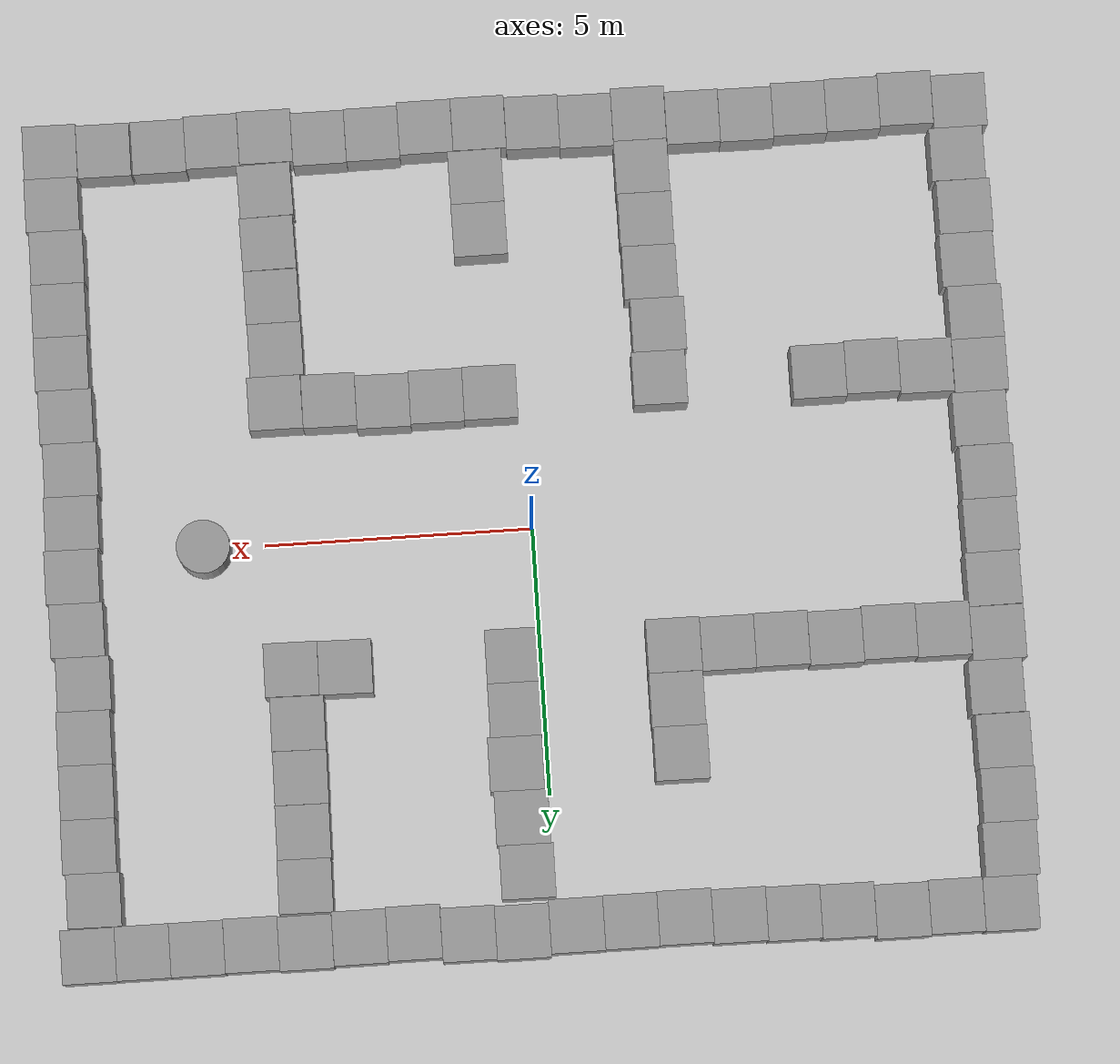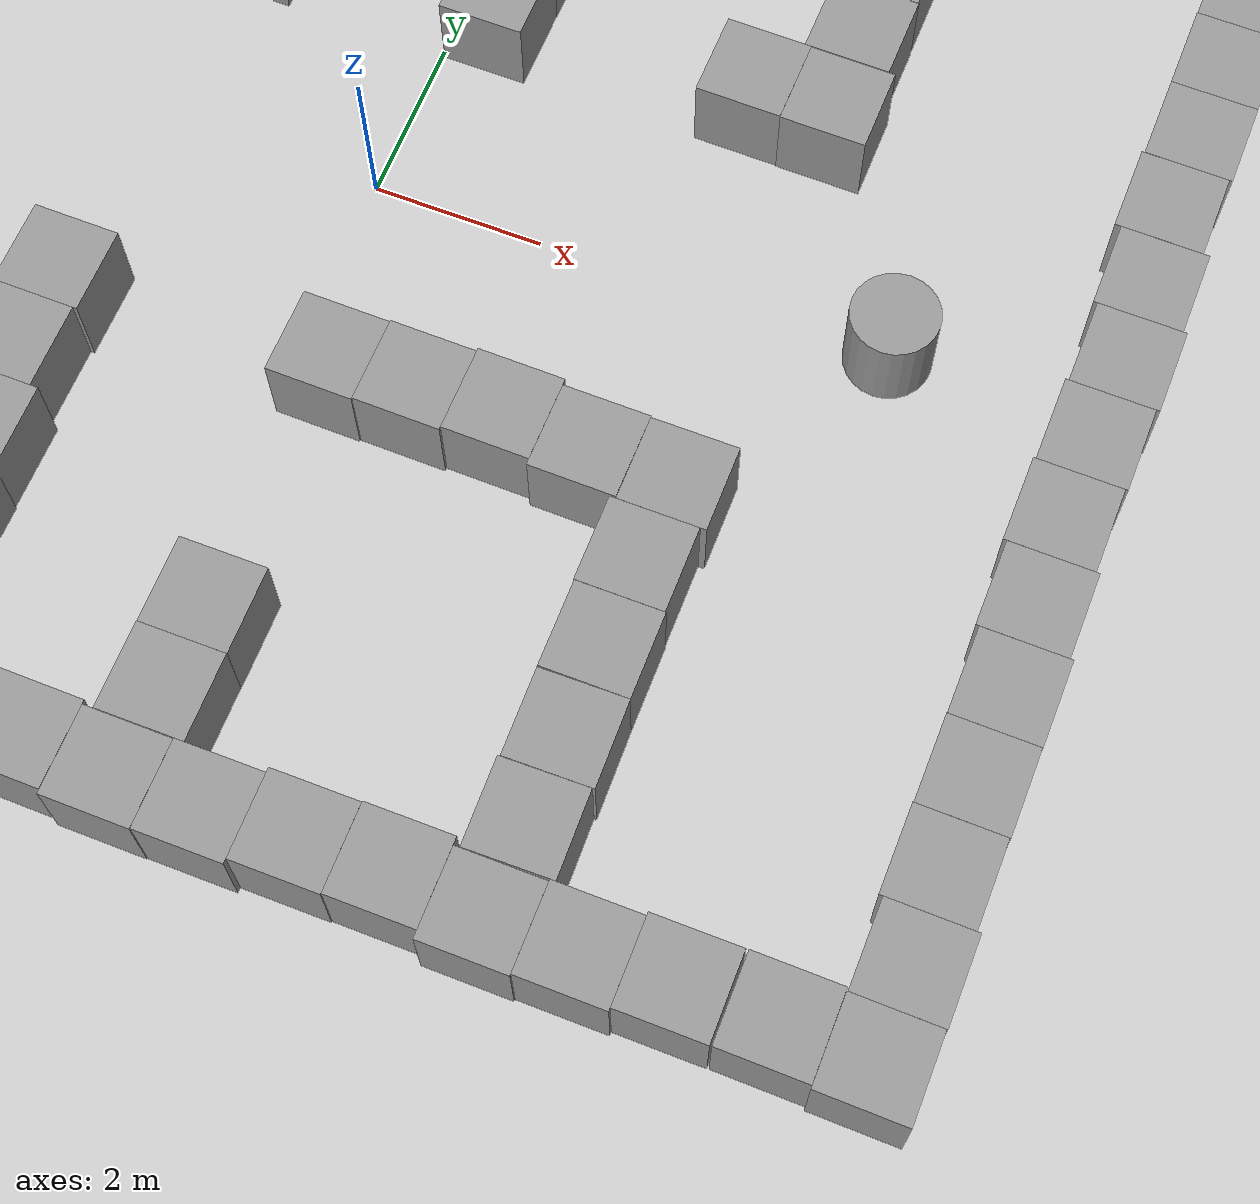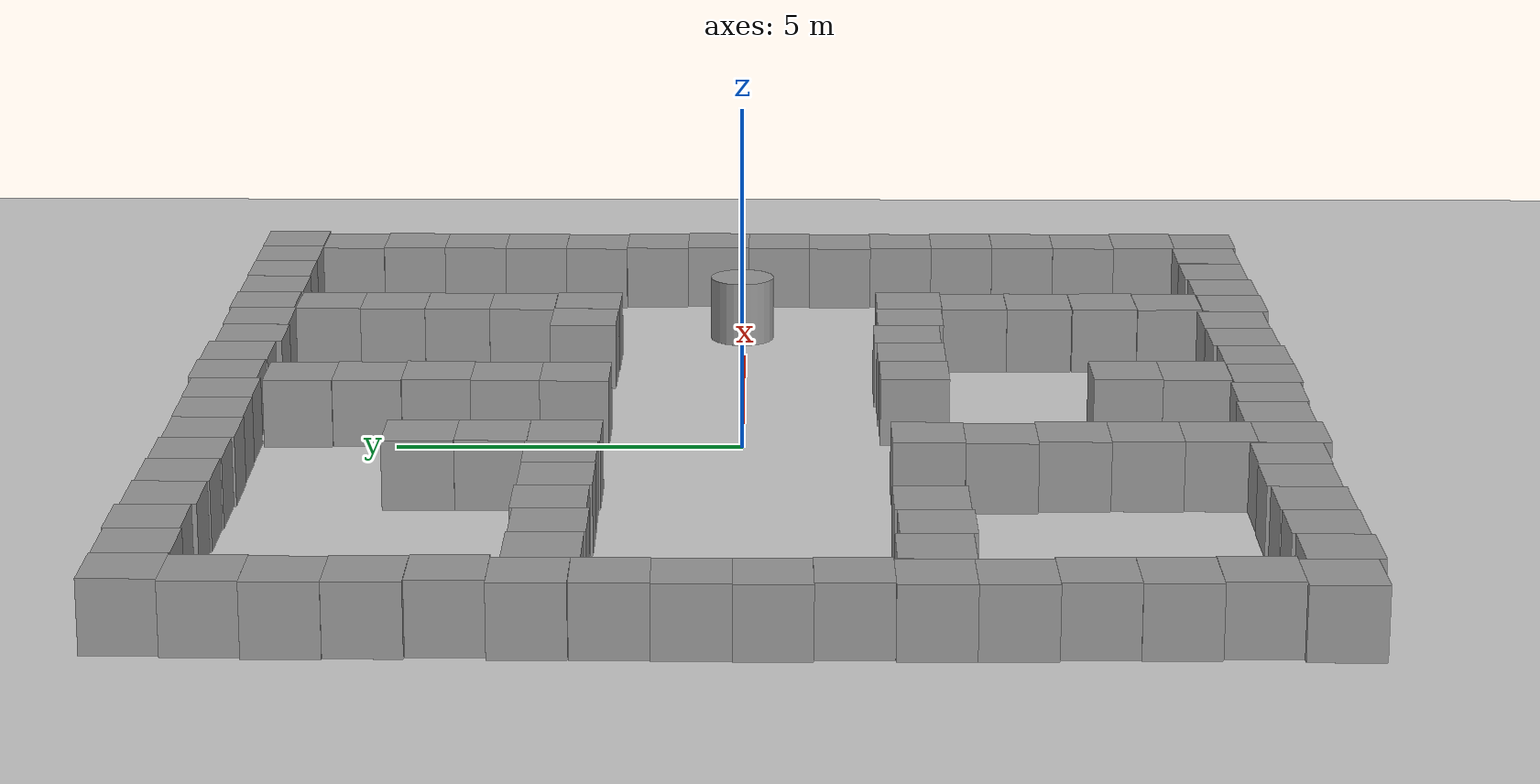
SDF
<sdf version="1.7">
 <world name="default">
  <light name="sun" type="directional">
   <pose>0 0 10 0 -0 0</pose>
   <diffuse>0.8 0.8 0.8 1</diffuse>
   <specular>0.2 0.2 0.2 1</specular>
   <attenuation>
    <range>1000</range>
    <constant>0.9</constant>
    <linear>0.01</linear>
    <quadratic>0.001</quadratic>
   </attenuation>
   <direction>-0.5 0.1 -0.9</direction>
   <spot><inner_angle>0</inner_angle><outer_angle>0</outer_angle><falloff>0</falloff></spot>
  </light>
  <model name="ground_plane">
   <static>1</static>
   <link name="link">
    <collision name="collision">
     <geometry><plane><normal>0 0 1</normal><size>100 100</size></plane></geometry>
     <surface>
      <contact><collide_bitmask>65535</collide_bitmask></contact>
      <friction><ode><mu>100</mu><mu2>50</mu2></ode></friction>
     </surface>
    </collision>
    <visual name="visual">
     <cast_shadows>0</cast_shadows>
     <geometry><plane><normal>0 0 1</normal><size>100 100</size></plane></geometry>
     <material>
      <script><uri>file://media/materials/scripts/gazebo.material</uri><name>Gazebo/Grey</name></script>
     </material>
    </visual>
   </link>
  </model>
  <gravity>0 0 -9.8</gravity>
  <magnetic_field>6e-06 2.3e-05 -4.2e-05</magnetic_field>
  <atmosphere type="adiabatic"/>
  <physics type="ode">
   <max_step_size>0.001</max_step_size>
   <real_time_factor>1</real_time_factor>
   <real_time_update_rate>1000</real_time_update_rate>
  </physics>
  <scene><ambient>0.4 0.4 0.4 1</ambient><background>0.7 0.7 0.7 1</background><shadows>1</shadows></scene>
  <spherical_coordinates>
   <surface_model>EARTH_WGS84</surface_model>
   <latitude_deg>0</latitude_deg>
   <longitude_deg>0</longitude_deg>
   <elevation>0</elevation>
   <heading_deg>0</heading_deg>
  </spherical_coordinates>
  <model name="unit_box">
   <pose>-1.48346 -7.49248 0.499995 1e-05 -0 -0.004181</pose>
   <link name="link">
    <inertial>
     <mass>1</mass>
     <inertia>
      <ixx>0.166667</ixx>
      <ixy>0</ixy>
      <ixz>0</ixz>
      <iyy>0.166667</iyy>
      <iyz>0</iyz>
      <izz>0.166667</izz>
     </inertia>
    </inertial>
    <collision name="collision"><geometry><box><size>1 1 1</size></box></geometry></collision>
    <visual name="visual">
     <geometry><box><size>1 1 1</size></box></geometry>
     <material>
      <script><name>Gazebo/Grey</name><uri>file://media/materials/scripts/gazebo.material</uri></script>
     </material>
    </visual>
   </link>
  </model>
  <model name="unit_box_clone">
   <pose>-0.483452 -7.53028 0.499995 1e-05 0 -0.003876</pose>
   <link name="link">
    <inertial>
     <mass>1</mass>
     <inertia>
      <ixx>0.166667</ixx>
      <ixy>0</ixy>
      <ixz>0</ixz>
      <iyy>0.166667</iyy>
      <iyz>0</iyz>
      <izz>0.166667</izz>
     </inertia>
    </inertial>
    <collision name="collision"><geometry><box><size>1 1 1</size></box></geometry></collision>
    <visual name="visual">
     <geometry><box><size>1 1 1</size></box></geometry>
     <material>
      <script><name>Gazebo/Grey</name><uri>file://media/materials/scripts/gazebo.material</uri></script>
     </material>
    </visual>
   </link>
  </model>
  <model name="unit_box_clone_0">
   <pose>0.519092 -7.5801 0.499995 -0 -1e-05 0.001579</pose>
   <link name="link">
    <inertial>
     <mass>1</mass>
     <inertia>
      <ixx>0.166667</ixx>
      <ixy>0</ixy>
      <ixz>0</ixz>
      <iyy>0.166667</iyy>
      <iyz>0</iyz>
      <izz>0.166667</izz>
     </inertia>
    </inertial>
    <collision name="collision"><geometry><box><size>1 1 1</size></box></geometry></collision>
    <visual name="visual">
     <geometry><box><size>1 1 1</size></box></geometry>
     <material>
      <script><name>Gazebo/Grey</name><uri>file://media/materials/scripts/gazebo.material</uri></script>
     </material>
    </visual>
   </link>
  </model>
  <model name="unit_box_clone_1">
   <pose>1.52066 -7.56872 0.499995 0 1e-05 0.004781</pose>
   <link name="link">
    <inertial>
     <mass>1</mass>
     <inertia>
      <ixx>0.166667</ixx>
      <ixy>0</ixy>
      <ixz>0</ixz>
      <iyy>0.166667</iyy>
      <iyz>0</iyz>
      <izz>0.166667</izz>
     </inertia>
    </inertial>
    <collision name="collision"><geometry><box><size>1 1 1</size></box></geometry></collision>
    <visual name="visual">
     <geometry><box><size>1 1 1</size></box></geometry>
     <material>
      <script><name>Gazebo/Grey</name><uri>file://media/materials/scripts/gazebo.material</uri></script>
     </material>
    </visual>
   </link>
  </model>
  <model name="unit_box_clone_2">
   <pose>2.52041 -7.50619 0.5 0 -0 0.004764</pose>
   <link name="link">
    <inertial>
     <mass>1</mass>
     <inertia>
      <ixx>0.166667</ixx>
      <ixy>0</ixy>
      <ixz>0</ixz>
      <iyy>0.166667</iyy>
      <iyz>0</iyz>
      <izz>0.166667</izz>
     </inertia>
    </inertial>
    <collision name="collision"><geometry><box><size>1 1 1</size></box></geometry></collision>
    <visual name="visual">
     <geometry><box><size>1 1 1</size></box></geometry>
     <material>
      <script><name>Gazebo/Grey</name><uri>file://media/materials/scripts/gazebo.material</uri></script>
     </material>
    </visual>
   </link>
  </model>
  <model name="unit_box_clone_3">
   <pose>3.521 -7.4896 0.499995 -1e-05 0 0.003476</pose>
   <link name="link">
    <inertial>
     <mass>1</mass>
     <inertia>
      <ixx>0.166667</ixx>
      <ixy>0</ixy>
      <ixz>0</ixz>
      <iyy>0.166667</iyy>
      <iyz>0</iyz>
      <izz>0.166667</izz>
     </inertia>
    </inertial>
    <collision name="collision"><geometry><box><size>1 1 1</size></box></geometry></collision>
    <visual name="visual">
     <geometry><box><size>1 1 1</size></box></geometry>
     <material>
      <script><name>Gazebo/Grey</name><uri>file://media/materials/scripts/gazebo.material</uri></script>
     </material>
    </visual>
   </link>
  </model>
  <model name="unit_box_clone_4">
   <pose>4.52182 -7.58155 0.5 0 -0 0.002312</pose>
   <link name="link">
    <inertial>
     <mass>1</mass>
     <inertia>
      <ixx>0.166667</ixx>
      <ixy>0</ixy>
      <ixz>0</ixz>
      <iyy>0.166667</iyy>
      <iyz>0</iyz>
      <izz>0.166667</izz>
     </inertia>
    </inertial>
    <collision name="collision"><geometry><box><size>1 1 1</size></box></geometry></collision>
    <visual name="visual">
     <geometry><box><size>1 1 1</size></box></geometry>
     <material>
      <script><name>Gazebo/Grey</name><uri>file://media/materials/scripts/gazebo.material</uri></script>
     </material>
    </visual>
   </link>
  </model>
  <model name="unit_box_clone_5">
   <pose>4.57544 -6.56698 0.499995 0 1e-05 0.020932</pose>
   <link name="link">
    <inertial>
     <mass>1</mass>
     <inertia>
      <ixx>0.166667</ixx>
      <ixy>0</ixy>
      <ixz>0</ixz>
      <iyy>0.166667</iyy>
      <iyz>0</iyz>
      <izz>0.166667</izz>
     </inertia>
    </inertial>
    <collision name="collision"><geometry><box><size>1 1 1</size></box></geometry></collision>
    <visual name="visual">
     <geometry><box><size>1 1 1</size></box></geometry>
     <material>
      <script><name>Gazebo/Grey</name><uri>file://media/materials/scripts/gazebo.material</uri></script>
     </material>
    </visual>
   </link>
  </model>
  <model name="unit_box_clone_6">
   <pose>4.5842 -5.56396 0.499995 0 -1e-05 0.016221</pose>
   <link name="link">
    <inertial>
     <mass>1</mass>
     <inertia>
      <ixx>0.166667</ixx>
      <ixy>0</ixy>
      <ixz>0</ixz>
      <iyy>0.166667</iyy>
      <iyz>0</iyz>
      <izz>0.166667</izz>
     </inertia>
    </inertial>
    <collision name="collision"><geometry><box><size>1 1 1</size></box></geometry></collision>
    <visual name="visual">
     <geometry><box><size>1 1 1</size></box></geometry>
     <material>
      <script><name>Gazebo/Grey</name><uri>file://media/materials/scripts/gazebo.material</uri></script>
     </material>
    </visual>
   </link>
  </model>
  <model name="unit_box_clone_7">
   <pose>4.57346 -4.5573 0.499995 -0 -1e-05 0.003007</pose>
   <link name="link">
    <inertial>
     <mass>1</mass>
     <inertia>
      <ixx>0.166667</ixx>
      <ixy>0</ixy>
      <ixz>0</ixz>
      <iyy>0.166667</iyy>
      <iyz>0</iyz>
      <izz>0.166667</izz>
     </inertia>
    </inertial>
    <collision name="collision"><geometry><box><size>1 1 1</size></box></geometry></collision>
    <visual name="visual">
     <geometry><box><size>1 1 1</size></box></geometry>
     <material>
      <script><name>Gazebo/Grey</name><uri>file://media/materials/scripts/gazebo.material</uri></script>
     </material>
    </visual>
   </link>
  </model>
  <model name="unit_box_clone_8">
   <pose>4.56116 -3.55637 0.499995 -1e-05 0 0.001132</pose>
   <link name="link">
    <inertial>
     <mass>1</mass>
     <inertia>
      <ixx>0.166667</ixx>
      <ixy>0</ixy>
      <ixz>0</ixz>
      <iyy>0.166667</iyy>
      <iyz>0</iyz>
      <izz>0.166667</izz>
     </inertia>
    </inertial>
    <collision name="collision"><geometry><box><size>1 1 1</size></box></geometry></collision>
    <visual name="visual">
     <geometry><box><size>1 1 1</size></box></geometry>
     <material>
      <script><name>Gazebo/Grey</name><uri>file://media/materials/scripts/gazebo.material</uri></script>
     </material>
    </visual>
   </link>
  </model>
  <model name="unit_box_clone_9">
   <pose>4.63155 -2.55598 0.5 0 -0 0.000421</pose>
   <link name="link">
    <inertial>
     <mass>1</mass>
     <inertia>
      <ixx>0.166667</ixx>
      <ixy>0</ixy>
      <ixz>0</ixz>
      <iyy>0.166667</iyy>
      <iyz>0</iyz>
      <izz>0.166667</izz>
     </inertia>
    </inertial>
    <collision name="collision"><geometry><box><size>1 1 1</size></box></geometry></collision>
    <visual name="visual">
     <geometry><box><size>1 1 1</size></box></geometry>
     <material>
      <script><name>Gazebo/Grey</name><uri>file://media/materials/scripts/gazebo.material</uri></script>
     </material>
    </visual>
   </link>
  </model>
  <model name="unit_box_clone_14">
   <pose>4.62729 2.42572 0.499995 0 1e-05 -0.011577</pose>
   <link name="link">
    <inertial>
     <mass>1</mass>
     <inertia>
      <ixx>0.166667</ixx>
      <ixy>0</ixy>
      <ixz>0</ixz>
      <iyy>0.166667</iyy>
      <iyz>0</iyz>
      <izz>0.166667</izz>
     </inertia>
    </inertial>
    <collision name="collision"><geometry><box><size>1 1 1</size></box></geometry></collision>
    <visual name="visual">
     <geometry><box><size>1 1 1</size></box></geometry>
     <material>
      <script><name>Gazebo/Grey</name><uri>file://media/materials/scripts/gazebo.material</uri></script>
     </material>
    </visual>
   </link>
  </model>
  <model name="unit_box_clone_15">
   <pose>4.56324 3.43446 0.499995 -1e-05 -0 -0.01434</pose>
   <link name="link">
    <inertial>
     <mass>1</mass>
     <inertia>
      <ixx>0.166667</ixx>
      <ixy>0</ixy>
      <ixz>0</ixz>
      <iyy>0.166667</iyy>
      <iyz>0</iyz>
      <izz>0.166667</izz>
     </inertia>
    </inertial>
    <collision name="collision"><geometry><box><size>1 1 1</size></box></geometry></collision>
    <visual name="visual">
     <geometry><box><size>1 1 1</size></box></geometry>
     <material>
      <script><name>Gazebo/Grey</name><uri>file://media/materials/scripts/gazebo.material</uri></script>
     </material>
    </visual>
   </link>
  </model>
  <model name="unit_box_clone_16">
   <pose>4.56989 4.436 0.499995 0 1e-05 -0.01189</pose>
   <link name="link">
    <inertial>
     <mass>1</mass>
     <inertia>
      <ixx>0.166667</ixx>
      <ixy>0</ixy>
      <ixz>0</ixz>
      <iyy>0.166667</iyy>
      <iyz>0</iyz>
      <izz>0.166667</izz>
     </inertia>
    </inertial>
    <collision name="collision"><geometry><box><size>1 1 1</size></box></geometry></collision>
    <visual name="visual">
     <geometry><box><size>1 1 1</size></box></geometry>
     <material>
      <script><name>Gazebo/Grey</name><uri>file://media/materials/scripts/gazebo.material</uri></script>
     </material>
    </visual>
   </link>
  </model>
  <model name="unit_box_clone_17">
   <pose>4.58635 5.43745 0.5 0 0 -0.010937</pose>
   <link name="link">
    <inertial>
     <mass>1</mass>
     <inertia>
      <ixx>0.166667</ixx>
      <ixy>0</ixy>
      <ixz>0</ixz>
      <iyy>0.166667</iyy>
      <iyz>0</iyz>
      <izz>0.166667</izz>
     </inertia>
    </inertial>
    <collision name="collision"><geometry><box><size>1 1 1</size></box></geometry></collision>
    <visual name="visual">
     <geometry><box><size>1 1 1</size></box></geometry>
     <material>
      <script><name>Gazebo/Grey</name><uri>file://media/materials/scripts/gazebo.material</uri></script>
     </material>
    </visual>
   </link>
  </model>
  <model name="unit_box_clone_18">
   <pose>4.60841 6.4373 0.499995 1e-05 -0 -0.010852</pose>
   <link name="link">
    <inertial>
     <mass>1</mass>
     <inertia>
      <ixx>0.166667</ixx>
      <ixy>0</ixy>
      <ixz>0</ixz>
      <iyy>0.166667</iyy>
      <iyz>0</iyz>
      <izz>0.166667</izz>
     </inertia>
    </inertial>
    <collision name="collision"><geometry><box><size>1 1 1</size></box></geometry></collision>
    <visual name="visual">
     <geometry><box><size>1 1 1</size></box></geometry>
     <material>
      <script><name>Gazebo/Grey</name><uri>file://media/materials/scripts/gazebo.material</uri></script>
     </material>
    </visual>
   </link>
  </model>
  <model name="unit_box_clone_19">
   <pose>4.66485 7.47334 0.499995 0 -1e-05 -0.000855</pose>
   <link name="link">
    <inertial>
     <mass>1</mass>
     <inertia>
      <ixx>0.166667</ixx>
      <ixy>0</ixy>
      <ixz>0</ixz>
      <iyy>0.166667</iyy>
      <iyz>0</iyz>
      <izz>0.166667</izz>
     </inertia>
    </inertial>
    <collision name="collision"><geometry><box><size>1 1 1</size></box></geometry></collision>
    <visual name="visual">
     <geometry><box><size>1 1 1</size></box></geometry>
     <material>
      <script><name>Gazebo/Grey</name><uri>file://media/materials/scripts/gazebo.material</uri></script>
     </material>
    </visual>
   </link>
  </model>
  <model name="unit_box_clone_20">
   <pose>3.66379 7.44276 0.499995 1e-05 -0 0.001076</pose>
   <link name="link">
    <inertial>
     <mass>1</mass>
     <inertia>
      <ixx>0.166667</ixx>
      <ixy>0</ixy>
      <ixz>0</ixz>
      <iyy>0.166667</iyy>
      <iyz>0</iyz>
      <izz>0.166667</izz>
     </inertia>
    </inertial>
    <collision name="collision"><geometry><box><size>1 1 1</size></box></geometry></collision>
    <visual name="visual">
     <geometry><box><size>1 1 1</size></box></geometry>
     <material>
      <script><name>Gazebo/Grey</name><uri>file://media/materials/scripts/gazebo.material</uri></script>
     </material>
    </visual>
   </link>
  </model>
  <model name="unit_box_clone_21">
   <pose>2.6637 7.42174 0.499995 -1e-05 0 0.000863</pose>
   <link name="link">
    <inertial>
     <mass>1</mass>
     <inertia>
      <ixx>0.166667</ixx>
      <ixy>0</ixy>
      <ixz>0</ixz>
      <iyy>0.166667</iyy>
      <iyz>0</iyz>
      <izz>0.166667</izz>
     </inertia>
    </inertial>
    <collision name="collision"><geometry><box><size>1 1 1</size></box></geometry></collision>
    <visual name="visual">
     <geometry><box><size>1 1 1</size></box></geometry>
     <material>
      <script><name>Gazebo/Grey</name><uri>file://media/materials/scripts/gazebo.material</uri></script>
     </material>
    </visual>
   </link>
  </model>
  <model name="unit_box_clone_22">
   <pose>1.66264 7.50897 0.499995 -1e-05 0 0.000387</pose>
   <link name="link">
    <inertial>
     <mass>1</mass>
     <inertia>
      <ixx>0.166667</ixx>
      <ixy>0</ixy>
      <ixz>0</ixz>
      <iyy>0.166667</iyy>
      <iyz>0</iyz>
      <izz>0.166667</izz>
     </inertia>
    </inertial>
    <collision name="collision"><geometry><box><size>1 1 1</size></box></geometry></collision>
    <visual name="visual">
     <geometry><box><size>1 1 1</size></box></geometry>
     <material>
      <script><name>Gazebo/Grey</name><uri>file://media/materials/scripts/gazebo.material</uri></script>
     </material>
    </visual>
   </link>
  </model>
  <model name="unit_box_clone_23">
   <pose>0.662513 7.53388 0.499995 1e-05 -0 0.000217</pose>
   <link name="link">
    <inertial>
     <mass>1</mass>
     <inertia>
      <ixx>0.166667</ixx>
      <ixy>0</ixy>
      <ixz>0</ixz>
      <iyy>0.166667</iyy>
      <iyz>0</iyz>
      <izz>0.166667</izz>
     </inertia>
    </inertial>
    <collision name="collision"><geometry><box><size>1 1 1</size></box></geometry></collision>
    <visual name="visual">
     <geometry><box><size>1 1 1</size></box></geometry>
     <material>
      <script><name>Gazebo/Grey</name><uri>file://media/materials/scripts/gazebo.material</uri></script>
     </material>
    </visual>
   </link>
  </model>
  <model name="unit_box_clone_24">
   <pose>-0.337977 7.47713 0.499995 -1e-05 -0 0.00065</pose>
   <link name="link">
    <inertial>
     <mass>1</mass>
     <inertia>
      <ixx>0.166667</ixx>
      <ixy>0</ixy>
      <ixz>0</ixz>
      <iyy>0.166667</iyy>
      <iyz>0</iyz>
      <izz>0.166667</izz>
     </inertia>
    </inertial>
    <collision name="collision"><geometry><box><size>1 1 1</size></box></geometry></collision>
    <visual name="visual">
     <geometry><box><size>1 1 1</size></box></geometry>
     <material>
      <script><name>Gazebo/Grey</name><uri>file://media/materials/scripts/gazebo.material</uri></script>
     </material>
    </visual>
   </link>
  </model>
  <model name="unit_box_clone_25">
   <pose>-1.33802 7.46853 0.5 0 -0 0.000596</pose>
   <link name="link">
    <inertial>
     <mass>1</mass>
     <inertia>
      <ixx>0.166667</ixx>
      <ixy>0</ixy>
      <ixz>0</ixz>
      <iyy>0.166667</iyy>
      <iyz>0</iyz>
      <izz>0.166667</izz>
     </inertia>
    </inertial>
    <collision name="collision"><geometry><box><size>1 1 1</size></box></geometry></collision>
    <visual name="visual">
     <geometry><box><size>1 1 1</size></box></geometry>
     <material>
      <script><name>Gazebo/Grey</name><uri>file://media/materials/scripts/gazebo.material</uri></script>
     </material>
    </visual>
   </link>
  </model>
  <model name="unit_box_clone_26">
   <pose>-2.33802 7.4561 0.5 0 -0 0.000584</pose>
   <link name="link">
    <inertial>
     <mass>1</mass>
     <inertia>
      <ixx>0.166667</ixx>
      <ixy>0</ixy>
      <ixz>0</ixz>
      <iyy>0.166667</iyy>
      <iyz>0</iyz>
      <izz>0.166667</izz>
     </inertia>
    </inertial>
    <collision name="collision"><geometry><box><size>1 1 1</size></box></geometry></collision>
    <visual name="visual">
     <geometry><box><size>1 1 1</size></box></geometry>
     <material>
      <script><name>Gazebo/Grey</name><uri>file://media/materials/scripts/gazebo.material</uri></script>
     </material>
    </visual>
   </link>
  </model>
  <model name="unit_box_clone_27">
   <pose>-3.33817 7.49082 0.5 0 -0 0.000326</pose>
   <link name="link">
    <inertial>
     <mass>1</mass>
     <inertia>
      <ixx>0.166667</ixx>
      <ixy>0</ixy>
      <ixz>0</ixz>
      <iyy>0.166667</iyy>
      <iyz>0</iyz>
      <izz>0.166667</izz>
     </inertia>
    </inertial>
    <collision name="collision"><geometry><box><size>1 1 1</size></box></geometry></collision>
    <visual name="visual">
     <geometry><box><size>1 1 1</size></box></geometry>
     <material>
      <script><name>Gazebo/Grey</name><uri>file://media/materials/scripts/gazebo.material</uri></script>
     </material>
    </visual>
   </link>
  </model>
  <model name="unit_box_clone_28">
   <pose>-4.33829 7.51118 0.5 0 -0 8.9e-05</pose>
   <link name="link">
    <inertial>
     <mass>1</mass>
     <inertia>
      <ixx>0.166667</ixx>
      <ixy>0</ixy>
      <ixz>0</ixz>
      <iyy>0.166667</iyy>
      <iyz>0</iyz>
      <izz>0.166667</izz>
     </inertia>
    </inertial>
    <collision name="collision"><geometry><box><size>1 1 1</size></box></geometry></collision>
    <visual name="visual">
     <geometry><box><size>1 1 1</size></box></geometry>
     <material>
      <script><name>Gazebo/Grey</name><uri>file://media/materials/scripts/gazebo.material</uri></script>
     </material>
    </visual>
   </link>
  </model>
  <model name="unit_box_clone_29">
   <pose>-5.3383 7.53597 0.499995 1e-05 0 6.8e-05</pose>
   <link name="link">
    <inertial>
     <mass>1</mass>
     <inertia>
      <ixx>0.166667</ixx>
      <ixy>0</ixy>
      <ixz>0</ixz>
      <iyy>0.166667</iyy>
      <iyz>0</iyz>
      <izz>0.166667</izz>
     </inertia>
    </inertial>
    <collision name="collision"><geometry><box><size>1 1 1</size></box></geometry></collision>
    <visual name="visual">
     <geometry><box><size>1 1 1</size></box></geometry>
     <material>
      <script><name>Gazebo/Grey</name><uri>file://media/materials/scripts/gazebo.material</uri></script>
     </material>
    </visual>
   </link>
  </model>
  <model name="unit_box_clone_30">
   <pose>-6.33833 7.60037 0.499995 1e-05 -0 1.4e-05</pose>
   <link name="link">
    <inertial>
     <mass>1</mass>
     <inertia>
      <ixx>0.166667</ixx>
      <ixy>0</ixy>
      <ixz>0</ixz>
      <iyy>0.166667</iyy>
      <iyz>0</iyz>
      <izz>0.166667</izz>
     </inertia>
    </inertial>
    <collision name="collision"><geometry><box><size>1 1 1</size></box></geometry></collision>
    <visual name="visual">
     <geometry><box><size>1 1 1</size></box></geometry>
     <material>
      <script><name>Gazebo/Grey</name><uri>file://media/materials/scripts/gazebo.material</uri></script>
     </material>
    </visual>
   </link>
  </model>
  <model name="unit_box_clone_31">
   <pose>-7.3384 7.57702 0.499995 0 -1e-05 -9.3e-05</pose>
   <link name="link">
    <inertial>
     <mass>1</mass>
     <inertia>
      <ixx>0.166667</ixx>
      <ixy>0</ixy>
      <ixz>0</ixz>
      <iyy>0.166667</iyy>
      <iyz>0</iyz>
      <izz>0.166667</izz>
     </inertia>
    </inertial>
    <collision name="collision"><geometry><box><size>1 1 1</size></box></geometry></collision>
    <visual name="visual">
     <geometry><box><size>1 1 1</size></box></geometry>
     <material>
      <script><name>Gazebo/Grey</name><uri>file://media/materials/scripts/gazebo.material</uri></script>
     </material>
    </visual>
   </link>
  </model>
  <model name="unit_box_clone_32">
   <pose>-8.33868 7.5929 0.499995 0 1e-05 -0.000708</pose>
   <link name="link">
    <inertial>
     <mass>1</mass>
     <inertia>
      <ixx>0.166667</ixx>
      <ixy>0</ixy>
      <ixz>0</ixz>
      <iyy>0.166667</iyy>
      <iyz>0</iyz>
      <izz>0.166667</izz>
     </inertia>
    </inertial>
    <collision name="collision"><geometry><box><size>1 1 1</size></box></geometry></collision>
    <visual name="visual">
     <geometry><box><size>1 1 1</size></box></geometry>
     <material>
      <script><name>Gazebo/Grey</name><uri>file://media/materials/scripts/gazebo.material</uri></script>
     </material>
    </visual>
   </link>
  </model>
  <model name="unit_box_clone_33">
   <pose>-8.40776 6.59292 0.499995 0 1e-05 -0.000748</pose>
   <link name="link">
    <inertial>
     <mass>1</mass>
     <inertia>
      <ixx>0.166667</ixx>
      <ixy>0</ixy>
      <ixz>0</ixz>
      <iyy>0.166667</iyy>
      <iyz>0</iyz>
      <izz>0.166667</izz>
     </inertia>
    </inertial>
    <collision name="collision"><geometry><box><size>1 1 1</size></box></geometry></collision>
    <visual name="visual">
     <geometry><box><size>1 1 1</size></box></geometry>
     <material>
      <script><name>Gazebo/Grey</name><uri>file://media/materials/scripts/gazebo.material</uri></script>
     </material>
    </visual>
   </link>
  </model>
  <model name="unit_box_clone_34">
   <pose>-8.44819 5.59252 0.5 -0 -0 -0.001683</pose>
   <link name="link">
    <inertial>
     <mass>1</mass>
     <inertia>
      <ixx>0.166667</ixx>
      <ixy>0</ixy>
      <ixz>0</ixz>
      <iyy>0.166667</iyy>
      <iyz>0</iyz>
      <izz>0.166667</izz>
     </inertia>
    </inertial>
    <collision name="collision"><geometry><box><size>1 1 1</size></box></geometry></collision>
    <visual name="visual">
     <geometry><box><size>1 1 1</size></box></geometry>
     <material>
      <script><name>Gazebo/Grey</name><uri>file://media/materials/scripts/gazebo.material</uri></script>
     </material>
    </visual>
   </link>
  </model>
  <model name="unit_box_clone_35">
   <pose>-8.43292 4.59249 0.499995 0 1e-05 -0.001692</pose>
   <link name="link">
    <inertial>
     <mass>1</mass>
     <inertia>
      <ixx>0.166667</ixx>
      <ixy>0</ixy>
      <ixz>0</ixz>
      <iyy>0.166667</iyy>
      <iyz>0</iyz>
      <izz>0.166667</izz>
     </inertia>
    </inertial>
    <collision name="collision"><geometry><box><size>1 1 1</size></box></geometry></collision>
    <visual name="visual">
     <geometry><box><size>1 1 1</size></box></geometry>
     <material>
      <script><name>Gazebo/Grey</name><uri>file://media/materials/scripts/gazebo.material</uri></script>
     </material>
    </visual>
   </link>
  </model>
  <model name="unit_box_clone_36">
   <pose>-8.37185 3.5869 0.499995 1e-05 -0 0.002115</pose>
   <link name="link">
    <inertial>
     <mass>1</mass>
     <inertia>
      <ixx>0.166667</ixx>
      <ixy>0</ixy>
      <ixz>0</ixz>
      <iyy>0.166667</iyy>
      <iyz>0</iyz>
      <izz>0.166667</izz>
     </inertia>
    </inertial>
    <collision name="collision"><geometry><box><size>1 1 1</size></box></geometry></collision>
    <visual name="visual">
     <geometry><box><size>1 1 1</size></box></geometry>
     <material>
      <script><name>Gazebo/Grey</name><uri>file://media/materials/scripts/gazebo.material</uri></script>
     </material>
    </visual>
   </link>
  </model>
  <model name="unit_box_clone_37">
   <pose>-8.4713 2.58632 0.499995 0 -1e-05 0.002251</pose>
   <link name="link">
    <inertial>
     <mass>1</mass>
     <inertia>
      <ixx>0.166667</ixx>
      <ixy>0</ixy>
      <ixz>0</ixz>
      <iyy>0.166667</iyy>
      <iyz>0</iyz>
      <izz>0.166667</izz>
     </inertia>
    </inertial>
    <collision name="collision"><geometry><box><size>1 1 1</size></box></geometry></collision>
    <visual name="visual">
     <geometry><box><size>1 1 1</size></box></geometry>
     <material>
      <script><name>Gazebo/Grey</name><uri>file://media/materials/scripts/gazebo.material</uri></script>
     </material>
    </visual>
   </link>
  </model>
  <model name="unit_box_clone_38">
   <pose>-8.46655 1.5814 0.499995 1e-05 -0 0.009421</pose>
   <link name="link">
    <inertial>
     <mass>1</mass>
     <inertia>
      <ixx>0.166667</ixx>
      <ixy>0</ixy>
      <ixz>0</ixz>
      <iyy>0.166667</iyy>
      <iyz>0</iyz>
      <izz>0.166667</izz>
     </inertia>
    </inertial>
    <collision name="collision"><geometry><box><size>1 1 1</size></box></geometry></collision>
    <visual name="visual">
     <geometry><box><size>1 1 1</size></box></geometry>
     <material>
      <script><name>Gazebo/Grey</name><uri>file://media/materials/scripts/gazebo.material</uri></script>
     </material>
    </visual>
   </link>
  </model>
  <model name="unit_box_clone_39">
   <pose>-8.49089 0.58107 0.499995 -1e-05 0 0.009286</pose>
   <link name="link">
    <inertial>
     <mass>1</mass>
     <inertia>
      <ixx>0.166667</ixx>
      <ixy>0</ixy>
      <ixz>0</ixz>
      <iyy>0.166667</iyy>
      <iyz>0</iyz>
      <izz>0.166667</izz>
     </inertia>
    </inertial>
    <collision name="collision"><geometry><box><size>1 1 1</size></box></geometry></collision>
    <visual name="visual">
     <geometry><box><size>1 1 1</size></box></geometry>
     <material>
      <script><name>Gazebo/Grey</name><uri>file://media/materials/scripts/gazebo.material</uri></script>
     </material>
    </visual>
   </link>
  </model>
  <model name="unit_box_clone_40">
   <pose>-8.50342 -0.419544 0.499995 1e-05 0 0.008373</pose>
   <link name="link">
    <inertial>
     <mass>1</mass>
     <inertia>
      <ixx>0.166667</ixx>
      <ixy>0</ixy>
      <ixz>0</ixz>
      <iyy>0.166667</iyy>
      <iyz>0</iyz>
      <izz>0.166667</izz>
     </inertia>
    </inertial>
    <collision name="collision"><geometry><box><size>1 1 1</size></box></geometry></collision>
    <visual name="visual">
     <geometry><box><size>1 1 1</size></box></geometry>
     <material>
      <script><name>Gazebo/Grey</name><uri>file://media/materials/scripts/gazebo.material</uri></script>
     </material>
    </visual>
   </link>
  </model>
  <model name="unit_box_clone_41">
   <pose>-8.44531 -1.42065 0.499995 0 1e-05 0.005312</pose>
   <link name="link">
    <inertial>
     <mass>1</mass>
     <inertia>
      <ixx>0.166667</ixx>
      <ixy>0</ixy>
      <ixz>0</ixz>
      <iyy>0.166667</iyy>
      <iyz>0</iyz>
      <izz>0.166667</izz>
     </inertia>
    </inertial>
    <collision name="collision"><geometry><box><size>1 1 1</size></box></geometry></collision>
    <visual name="visual">
     <geometry><box><size>1 1 1</size></box></geometry>
     <material>
      <script><name>Gazebo/Grey</name><uri>file://media/materials/scripts/gazebo.material</uri></script>
     </material>
    </visual>
   </link>
  </model>
  <model name="unit_box_clone_42">
   <pose>-8.50894 -2.42112 0.499995 0 -1e-05 0.005258</pose>
   <link name="link">
    <inertial>
     <mass>1</mass>
     <inertia>
      <ixx>0.166667</ixx>
      <ixy>0</ixy>
      <ixz>0</ixz>
      <iyy>0.166667</iyy>
      <iyz>0</iyz>
      <izz>0.166667</izz>
     </inertia>
    </inertial>
    <collision name="collision"><geometry><box><size>1 1 1</size></box></geometry></collision>
    <visual name="visual">
     <geometry><box><size>1 1 1</size></box></geometry>
     <material>
      <script><name>Gazebo/Grey</name><uri>file://media/materials/scripts/gazebo.material</uri></script>
     </material>
    </visual>
   </link>
  </model>
  <model name="unit_box_clone_43">
   <pose>-8.50524 -3.42113 0.499995 -0 -1e-05 0.005234</pose>
   <link name="link">
    <inertial>
     <mass>1</mass>
     <inertia>
      <ixx>0.166667</ixx>
      <ixy>0</ixy>
      <ixz>0</ixz>
      <iyy>0.166667</iyy>
      <iyz>0</iyz>
      <izz>0.166667</izz>
     </inertia>
    </inertial>
    <collision name="collision"><geometry><box><size>1 1 1</size></box></geometry></collision>
    <visual name="visual">
     <geometry><box><size>1 1 1</size></box></geometry>
     <material>
      <script><name>Gazebo/Grey</name><uri>file://media/materials/scripts/gazebo.material</uri></script>
     </material>
    </visual>
   </link>
  </model>
  <model name="unit_box_clone_44">
   <pose>-8.42681 -4.42082 0.499995 -0 -1e-05 0.005078</pose>
   <link name="link">
    <inertial>
     <mass>1</mass>
     <inertia>
      <ixx>0.166667</ixx>
      <ixy>0</ixy>
      <ixz>0</ixz>
      <iyy>0.166667</iyy>
      <iyz>0</iyz>
      <izz>0.166667</izz>
     </inertia>
    </inertial>
    <collision name="collision"><geometry><box><size>1 1 1</size></box></geometry></collision>
    <visual name="visual">
     <geometry><box><size>1 1 1</size></box></geometry>
     <material>
      <script><name>Gazebo/Grey</name><uri>file://media/materials/scripts/gazebo.material</uri></script>
     </material>
    </visual>
   </link>
  </model>
  <model name="unit_box_clone_45">
   <pose>-8.44626 -5.42149 0.499995 0 -1e-05 0.00396</pose>
   <link name="link">
    <inertial>
     <mass>1</mass>
     <inertia>
      <ixx>0.166667</ixx>
      <ixy>0</ixy>
      <ixz>0</ixz>
      <iyy>0.166667</iyy>
      <iyz>0</iyz>
      <izz>0.166667</izz>
     </inertia>
    </inertial>
    <collision name="collision"><geometry><box><size>1 1 1</size></box></geometry></collision>
    <visual name="visual">
     <geometry><box><size>1 1 1</size></box></geometry>
     <material>
      <script><name>Gazebo/Grey</name><uri>file://media/materials/scripts/gazebo.material</uri></script>
     </material>
    </visual>
   </link>
  </model>
  <model name="unit_box_clone_46">
   <pose>-8.38158 -6.42358 0.499995 -0 -1e-05 -0.000724</pose>
   <link name="link">
    <inertial>
     <mass>1</mass>
     <inertia>
      <ixx>0.166667</ixx>
      <ixy>0</ixy>
      <ixz>0</ixz>
      <iyy>0.166667</iyy>
      <iyz>0</iyz>
      <izz>0.166667</izz>
     </inertia>
    </inertial>
    <collision name="collision"><geometry><box><size>1 1 1</size></box></geometry></collision>
    <visual name="visual">
     <geometry><box><size>1 1 1</size></box></geometry>
     <material>
      <script><name>Gazebo/Grey</name><uri>file://media/materials/scripts/gazebo.material</uri></script>
     </material>
    </visual>
   </link>
  </model>
  <model name="unit_box_clone_47">
   <pose>-8.48809 -7.4237 0.499995 -1e-05 -0 -0.001166</pose>
   <link name="link">
    <inertial>
     <mass>1</mass>
     <inertia>
      <ixx>0.166667</ixx>
      <ixy>0</ixy>
      <ixz>0</ixz>
      <iyy>0.166667</iyy>
      <iyz>0</iyz>
      <izz>0.166667</izz>
     </inertia>
    </inertial>
    <collision name="collision"><geometry><box><size>1 1 1</size></box></geometry></collision>
    <visual name="visual">
     <geometry><box><size>1 1 1</size></box></geometry>
     <material>
      <script><name>Gazebo/Grey</name><uri>file://media/materials/scripts/gazebo.material</uri></script>
     </material>
    </visual>
   </link>
  </model>
  <model name="unit_box_clone_48">
   <pose>-7.48748 -7.52979 0.5 0 0 -0.003001</pose>
   <link name="link">
    <inertial>
     <mass>1</mass>
     <inertia>
      <ixx>0.166667</ixx>
      <ixy>0</ixy>
      <ixz>0</ixz>
      <iyy>0.166667</iyy>
      <iyz>0</iyz>
      <izz>0.166667</izz>
     </inertia>
    </inertial>
    <collision name="collision"><geometry><box><size>1 1 1</size></box></geometry></collision>
    <visual name="visual">
     <geometry><box><size>1 1 1</size></box></geometry>
     <material>
      <script><name>Gazebo/Grey</name><uri>file://media/materials/scripts/gazebo.material</uri></script>
     </material>
    </visual>
   </link>
  </model>
  <model name="unit_box_clone_49">
   <pose>-6.48721 -7.48332 0.499995 1e-05 -0 -0.003242</pose>
   <link name="link">
    <inertial>
     <mass>1</mass>
     <inertia>
      <ixx>0.166667</ixx>
      <ixy>0</ixy>
      <ixz>0</ixz>
      <iyy>0.166667</iyy>
      <iyz>0</iyz>
      <izz>0.166667</izz>
     </inertia>
    </inertial>
    <collision name="collision"><geometry><box><size>1 1 1</size></box></geometry></collision>
    <visual name="visual">
     <geometry><box><size>1 1 1</size></box></geometry>
     <material>
      <script><name>Gazebo/Grey</name><uri>file://media/materials/scripts/gazebo.material</uri></script>
     </material>
    </visual>
   </link>
  </model>
  <model name="unit_box_clone_50">
   <pose>-5.48713 -7.4684 0.499995 1e-05 -0 -0.003279</pose>
   <link name="link">
    <inertial>
     <mass>1</mass>
     <inertia>
      <ixx>0.166667</ixx>
      <ixy>0</ixy>
      <ixz>0</ixz>
      <iyy>0.166667</iyy>
      <iyz>0</iyz>
      <izz>0.166667</izz>
     </inertia>
    </inertial>
    <collision name="collision"><geometry><box><size>1 1 1</size></box></geometry></collision>
    <visual name="visual">
     <geometry><box><size>1 1 1</size></box></geometry>
     <material>
      <script><name>Gazebo/Grey</name><uri>file://media/materials/scripts/gazebo.material</uri></script>
     </material>
    </visual>
   </link>
  </model>
  <model name="unit_box_clone_51">
   <pose>-4.48697 -7.4217 0.499995 -1e-05 -0 -0.003279</pose>
   <link name="link">
    <inertial>
     <mass>1</mass>
     <inertia>
      <ixx>0.166667</ixx>
      <ixy>0</ixy>
      <ixz>0</ixz>
      <iyy>0.166667</iyy>
      <iyz>0</iyz>
      <izz>0.166667</izz>
     </inertia>
    </inertial>
    <collision name="collision"><geometry><box><size>1 1 1</size></box></geometry></collision>
    <visual name="visual">
     <geometry><box><size>1 1 1</size></box></geometry>
     <material>
      <script><name>Gazebo/Grey</name><uri>file://media/materials/scripts/gazebo.material</uri></script>
     </material>
    </visual>
   </link>
  </model>
  <model name="unit_box_clone_52">
   <pose>-3.48641 -7.43676 0.499995 -1e-05 -0 -0.003485</pose>
   <link name="link">
    <inertial>
     <mass>1</mass>
     <inertia>
      <ixx>0.166667</ixx>
      <ixy>0</ixy>
      <ixz>0</ixz>
      <iyy>0.166667</iyy>
      <iyz>0</iyz>
      <izz>0.166667</izz>
     </inertia>
    </inertial>
    <collision name="collision"><geometry><box><size>1 1 1</size></box></geometry></collision>
    <visual name="visual">
     <geometry><box><size>1 1 1</size></box></geometry>
     <material>
      <script><name>Gazebo/Grey</name><uri>file://media/materials/scripts/gazebo.material</uri></script>
     </material>
    </visual>
   </link>
  </model>
  <model name="unit_box_clone_53">
   <pose>-2.48441 -7.56762 0.499995 -1e-05 -0 -0.002841</pose>
   <link name="link">
    <inertial>
     <mass>1</mass>
     <inertia>
      <ixx>0.166667</ixx>
      <ixy>0</ixy>
      <ixz>0</ixz>
      <iyy>0.166667</iyy>
      <iyz>0</iyz>
      <izz>0.166667</izz>
     </inertia>
    </inertial>
    <collision name="collision"><geometry><box><size>1 1 1</size></box></geometry></collision>
    <visual name="visual">
     <geometry><box><size>1 1 1</size></box></geometry>
     <material>
      <script><name>Gazebo/Grey</name><uri>file://media/materials/scripts/gazebo.material</uri></script>
     </material>
    </visual>
   </link>
  </model>
  <model name="unit_box_0">
   <pose>-2.47958 -6.56694 0.499995 1e-05 -0 -0.004236</pose>
   <link name="link">
    <inertial>
     <mass>1</mass>
     <inertia>
      <ixx>0.166667</ixx>
      <ixy>0</ixy>
      <ixz>0</ixz>
      <iyy>0.166667</iyy>
      <iyz>0</iyz>
      <izz>0.166667</izz>
     </inertia>
    </inertial>
    <collision name="collision"><geometry><box><size>1 1 1</size></box></geometry></collision>
    <visual name="visual">
     <geometry><box><size>1 1 1</size></box></geometry>
     <material>
      <script><name>Gazebo/Grey</name><uri>file://media/materials/scripts/gazebo.material</uri></script>
     </material>
    </visual>
   </link>
  </model>
  <model name="unit_box_clone_10">
   <pose>-2.48697 -5.56654 0.499995 0 -1e-05 -0.003532</pose>
   <link name="link">
    <inertial>
     <mass>1</mass>
     <inertia>
      <ixx>0.166667</ixx>
      <ixy>0</ixy>
      <ixz>0</ixz>
      <iyy>0.166667</iyy>
      <iyz>0</iyz>
      <izz>0.166667</izz>
     </inertia>
    </inertial>
    <collision name="collision"><geometry><box><size>1 1 1</size></box></geometry></collision>
    <visual name="visual">
     <geometry><box><size>1 1 1</size></box></geometry>
     <material>
      <script><name>Gazebo/Grey</name><uri>file://media/materials/scripts/gazebo.material</uri></script>
     </material>
    </visual>
   </link>
  </model>
  <model name="unit_box_clone_11">
   <pose>-2.49776 -4.56632 0.499995 0 -1e-05 -0.003193</pose>
   <link name="link">
    <inertial>
     <mass>1</mass>
     <inertia>
      <ixx>0.166667</ixx>
      <ixy>0</ixy>
      <ixz>0</ixz>
      <iyy>0.166667</iyy>
      <iyz>0</iyz>
      <izz>0.166667</izz>
     </inertia>
    </inertial>
    <collision name="collision"><geometry><box><size>1 1 1</size></box></geometry></collision>
    <visual name="visual">
     <geometry><box><size>1 1 1</size></box></geometry>
     <material>
      <script><name>Gazebo/Grey</name><uri>file://media/materials/scripts/gazebo.material</uri></script>
     </material>
    </visual>
   </link>
  </model>
  <model name="unit_box_clone_12">
   <pose>-7.50591 -2.4638 0.499995 -1e-05 -0 -0.000847</pose>
   <link name="link">
    <inertial>
     <mass>1</mass>
     <inertia>
      <ixx>0.166667</ixx>
      <ixy>0</ixy>
      <ixz>0</ixz>
      <iyy>0.166667</iyy>
      <iyz>0</iyz>
      <izz>0.166667</izz>
     </inertia>
    </inertial>
    <collision name="collision"><geometry><box><size>1 1 1</size></box></geometry></collision>
    <visual name="visual">
     <geometry><box><size>1 1 1</size></box></geometry>
     <material>
      <script><name>Gazebo/Grey</name><uri>file://media/materials/scripts/gazebo.material</uri></script>
     </material>
    </visual>
   </link>
  </model>
  <model name="unit_box_clone_13">
   <pose>-6.50583 -2.52671 0.5 0 0 -0.001139</pose>
   <link name="link">
    <inertial>
     <mass>1</mass>
     <inertia>
      <ixx>0.166667</ixx>
      <ixy>0</ixy>
      <ixz>0</ixz>
      <iyy>0.166667</iyy>
      <iyz>0</iyz>
      <izz>0.166667</izz>
     </inertia>
    </inertial>
    <collision name="collision"><geometry><box><size>1 1 1</size></box></geometry></collision>
    <visual name="visual">
     <geometry><box><size>1 1 1</size></box></geometry>
     <material>
      <script><name>Gazebo/Grey</name><uri>file://media/materials/scripts/gazebo.material</uri></script>
     </material>
    </visual>
   </link>
  </model>
  <model name="unit_box_clone_54">
   <pose>-2.58935 -3.56579 0.499995 -0 1e-05 -0.003501</pose>
   <link name="link">
    <inertial>
     <mass>1</mass>
     <inertia>
      <ixx>0.166667</ixx>
      <ixy>0</ixy>
      <ixz>0</ixz>
      <iyy>0.166667</iyy>
      <iyz>0</iyz>
      <izz>0.166667</izz>
     </inertia>
    </inertial>
    <collision name="collision"><geometry><box><size>1 1 1</size></box></geometry></collision>
    <visual name="visual">
     <geometry><box><size>1 1 1</size></box></geometry>
     <material>
      <script><name>Gazebo/Grey</name><uri>file://media/materials/scripts/gazebo.material</uri></script>
     </material>
    </visual>
   </link>
  </model>
  <model name="unit_box_clone_55">
   <pose>-2.54254 -2.56583 0.5 0 -0 -0.003565</pose>
   <link name="link">
    <inertial>
     <mass>1</mass>
     <inertia>
      <ixx>0.166667</ixx>
      <ixy>0</ixy>
      <ixz>0</ixz>
      <iyy>0.166667</iyy>
      <iyz>0</iyz>
      <izz>0.166667</izz>
     </inertia>
    </inertial>
    <collision name="collision"><geometry><box><size>1 1 1</size></box></geometry></collision>
    <visual name="visual">
     <geometry><box><size>1 1 1</size></box></geometry>
     <material>
      <script><name>Gazebo/Grey</name><uri>file://media/materials/scripts/gazebo.material</uri></script>
     </material>
    </visual>
   </link>
  </model>
  <model name="unit_box_clone_56">
   <pose>-5.50578 -2.49302 0.5 -0 -0 -0.001165</pose>
   <link name="link">
    <inertial>
     <mass>1</mass>
     <inertia>
      <ixx>0.166667</ixx>
      <ixy>0</ixy>
      <ixz>0</ixz>
      <iyy>0.166667</iyy>
      <iyz>0</iyz>
      <izz>0.166667</izz>
     </inertia>
    </inertial>
    <collision name="collision"><geometry><box><size>1 1 1</size></box></geometry></collision>
    <visual name="visual">
     <geometry><box><size>1 1 1</size></box></geometry>
     <material>
      <script><name>Gazebo/Grey</name><uri>file://media/materials/scripts/gazebo.material</uri></script>
     </material>
    </visual>
   </link>
  </model>
  <model name="unit_box_clone_57">
   <pose>-7.47026 2.46496 0.499995 0 1e-05 0.000256</pose>
   <link name="link">
    <inertial>
     <mass>1</mass>
     <inertia>
      <ixx>0.166667</ixx>
      <ixy>0</ixy>
      <ixz>0</ixz>
      <iyy>0.166667</iyy>
      <iyz>0</iyz>
      <izz>0.166667</izz>
     </inertia>
    </inertial>
    <collision name="collision"><geometry><box><size>1 1 1</size></box></geometry></collision>
    <visual name="visual">
     <geometry><box><size>1 1 1</size></box></geometry>
     <material>
      <script><name>Gazebo/Grey</name><uri>file://media/materials/scripts/gazebo.material</uri></script>
     </material>
    </visual>
   </link>
  </model>
  <model name="unit_box_clone_58">
   <pose>-6.47022 2.44267 0.499995 0 1e-05 0.000209</pose>
   <link name="link">
    <inertial>
     <mass>1</mass>
     <inertia>
      <ixx>0.166667</ixx>
      <ixy>0</ixy>
      <ixz>0</ixz>
      <iyy>0.166667</iyy>
      <iyz>0</iyz>
      <izz>0.166667</izz>
     </inertia>
    </inertial>
    <collision name="collision"><geometry><box><size>1 1 1</size></box></geometry></collision>
    <visual name="visual">
     <geometry><box><size>1 1 1</size></box></geometry>
     <material>
      <script><name>Gazebo/Grey</name><uri>file://media/materials/scripts/gazebo.material</uri></script>
     </material>
    </visual>
   </link>
  </model>
  <model name="unit_box_clone_59">
   <pose>-5.47023 2.48317 0.499995 0 1e-05 0.000209</pose>
   <link name="link">
    <inertial>
     <mass>1</mass>
     <inertia>
      <ixx>0.166667</ixx>
      <ixy>0</ixy>
      <ixz>0</ixz>
      <iyy>0.166667</iyy>
      <iyz>0</iyz>
      <izz>0.166667</izz>
     </inertia>
    </inertial>
    <collision name="collision"><geometry><box><size>1 1 1</size></box></geometry></collision>
    <visual name="visual">
     <geometry><box><size>1 1 1</size></box></geometry>
     <material>
      <script><name>Gazebo/Grey</name><uri>file://media/materials/scripts/gazebo.material</uri></script>
     </material>
    </visual>
   </link>
  </model>
  <model name="unit_box_clone_60">
   <pose>-4.47014 2.44971 0.499995 -0 1e-05 5.6e-05</pose>
   <link name="link">
    <inertial>
     <mass>1</mass>
     <inertia>
      <ixx>0.166667</ixx>
      <ixy>0</ixy>
      <ixz>0</ixz>
      <iyy>0.166667</iyy>
      <iyz>0</iyz>
      <izz>0.166667</izz>
     </inertia>
    </inertial>
    <collision name="collision"><geometry><box><size>1 1 1</size></box></geometry></collision>
    <visual name="visual">
     <geometry><box><size>1 1 1</size></box></geometry>
     <material>
      <script><name>Gazebo/Grey</name><uri>file://media/materials/scripts/gazebo.material</uri></script>
     </material>
    </visual>
   </link>
  </model>
  <model name="unit_box_clone_61">
   <pose>-3.47009 2.4573 0.499995 1e-05 -0 -3.4e-05</pose>
   <link name="link">
    <inertial>
     <mass>1</mass>
     <inertia>
      <ixx>0.166667</ixx>
      <ixy>0</ixy>
      <ixz>0</ixz>
      <iyy>0.166667</iyy>
      <iyz>0</iyz>
      <izz>0.166667</izz>
     </inertia>
    </inertial>
    <collision name="collision"><geometry><box><size>1 1 1</size></box></geometry></collision>
    <visual name="visual">
     <geometry><box><size>1 1 1</size></box></geometry>
     <material>
      <script><name>Gazebo/Grey</name><uri>file://media/materials/scripts/gazebo.material</uri></script>
     </material>
    </visual>
   </link>
  </model>
  <model name="unit_box_clone_62">
   <pose>-2.46974 2.43367 0.499995 -1e-05 0 -0.000763</pose>
   <link name="link">
    <inertial>
     <mass>1</mass>
     <inertia>
      <ixx>0.166667</ixx>
      <ixy>0</ixy>
      <ixz>0</ixz>
      <iyy>0.166667</iyy>
      <iyz>0</iyz>
      <izz>0.166667</izz>
     </inertia>
    </inertial>
    <collision name="collision"><geometry><box><size>1 1 1</size></box></geometry></collision>
    <visual name="visual">
     <geometry><box><size>1 1 1</size></box></geometry>
     <material>
      <script><name>Gazebo/Grey</name><uri>file://media/materials/scripts/gazebo.material</uri></script>
     </material>
    </visual>
   </link>
  </model>
  <model name="unit_box_clone_63">
   <pose>-2.46473 3.4355 0.499995 1e-05 -0 -0.004451</pose>
   <link name="link">
    <inertial>
     <mass>1</mass>
     <inertia>
      <ixx>0.166667</ixx>
      <ixy>0</ixy>
      <ixz>0</ixz>
      <iyy>0.166667</iyy>
      <iyz>0</iyz>
      <izz>0.166667</izz>
     </inertia>
    </inertial>
    <collision name="collision"><geometry><box><size>1 1 1</size></box></geometry></collision>
    <visual name="visual">
     <geometry><box><size>1 1 1</size></box></geometry>
     <material>
      <script><name>Gazebo/Grey</name><uri>file://media/materials/scripts/gazebo.material</uri></script>
     </material>
    </visual>
   </link>
  </model>
  <model name="unit_box_clone_64">
   <pose>-2.47623 4.43564 0.499995 1e-05 -0 -0.0046</pose>
   <link name="link">
    <inertial>
     <mass>1</mass>
     <inertia>
      <ixx>0.166667</ixx>
      <ixy>0</ixy>
      <ixz>0</ixz>
      <iyy>0.166667</iyy>
      <iyz>0</iyz>
      <izz>0.166667</izz>
     </inertia>
    </inertial>
    <collision name="collision"><geometry><box><size>1 1 1</size></box></geometry></collision>
    <visual name="visual">
     <geometry><box><size>1 1 1</size></box></geometry>
     <material>
      <script><name>Gazebo/Grey</name><uri>file://media/materials/scripts/gazebo.material</uri></script>
     </material>
    </visual>
   </link>
  </model>
  <model name="unit_box_clone_65">
   <pose>0.628847 -6.57333 0.499995 1e-05 -0 0.005777</pose>
   <link name="link">
    <inertial>
     <mass>1</mass>
     <inertia>
      <ixx>0.166667</ixx>
      <ixy>0</ixy>
      <ixz>0</ixz>
      <iyy>0.166667</iyy>
      <iyz>0</iyz>
      <izz>0.166667</izz>
     </inertia>
    </inertial>
    <collision name="collision"><geometry><box><size>1 1 1</size></box></geometry></collision>
    <visual name="visual">
     <geometry><box><size>1 1 1</size></box></geometry>
     <material>
      <script><name>Gazebo/Grey</name><uri>file://media/materials/scripts/gazebo.material</uri></script>
     </material>
    </visual>
   </link>
  </model>
  <model name="unit_box_clone_66">
   <pose>0.627772 -5.5733 0.499995 -1e-05 0 0.005779</pose>
   <link name="link">
    <inertial>
     <mass>1</mass>
     <inertia>
      <ixx>0.166667</ixx>
      <ixy>0</ixy>
      <ixz>0</ixz>
      <iyy>0.166667</iyy>
      <iyz>0</iyz>
      <izz>0.166667</izz>
     </inertia>
    </inertial>
    <collision name="collision"><geometry><box><size>1 1 1</size></box></geometry></collision>
    <visual name="visual">
     <geometry><box><size>1 1 1</size></box></geometry>
     <material>
      <script><name>Gazebo/Grey</name><uri>file://media/materials/scripts/gazebo.material</uri></script>
     </material>
    </visual>
   </link>
  </model>
  <model name="unit_box_clone_67">
   <pose>3.62829 -2.53701 0.499995 0 1e-05 -0.006264</pose>
   <link name="link">
    <inertial>
     <mass>1</mass>
     <inertia>
      <ixx>0.166667</ixx>
      <ixy>0</ixy>
      <ixz>0</ixz>
      <iyy>0.166667</iyy>
      <iyz>0</iyz>
      <izz>0.166667</izz>
     </inertia>
    </inertial>
    <collision name="collision"><geometry><box><size>1 1 1</size></box></geometry></collision>
    <visual name="visual">
     <geometry><box><size>1 1 1</size></box></geometry>
     <material>
      <script><name>Gazebo/Grey</name><uri>file://media/materials/scripts/gazebo.material</uri></script>
     </material>
    </visual>
   </link>
  </model>
  <model name="unit_box_clone_68">
   <pose>2.62789 -2.46035 0.499995 0 1e-05 -0.008263</pose>
   <link name="link">
    <inertial>
     <mass>1</mass>
     <inertia>
      <ixx>0.166667</ixx>
      <ixy>0</ixy>
      <ixz>0</ixz>
      <iyy>0.166667</iyy>
      <iyz>0</iyz>
      <izz>0.166667</izz>
     </inertia>
    </inertial>
    <collision name="collision"><geometry><box><size>1 1 1</size></box></geometry></collision>
    <visual name="visual">
     <geometry><box><size>1 1 1</size></box></geometry>
     <material>
      <script><name>Gazebo/Grey</name><uri>file://media/materials/scripts/gazebo.material</uri></script>
     </material>
    </visual>
   </link>
  </model>
  <model name="unit_box_clone_69">
   <pose>1.6276 -2.48699 0.499995 1e-05 -0 -0.008301</pose>
   <link name="link">
    <inertial>
     <mass>1</mass>
     <inertia>
      <ixx>0.166667</ixx>
      <ixy>0</ixy>
      <ixz>0</ixz>
      <iyy>0.166667</iyy>
      <iyz>0</iyz>
      <izz>0.166667</izz>
     </inertia>
    </inertial>
    <collision name="collision"><geometry><box><size>1 1 1</size></box></geometry></collision>
    <visual name="visual">
     <geometry><box><size>1 1 1</size></box></geometry>
     <material>
      <script><name>Gazebo/Grey</name><uri>file://media/materials/scripts/gazebo.material</uri></script>
     </material>
    </visual>
   </link>
  </model>
  <model name="unit_box_clone_70">
   <pose>0.627459 -2.49583 0.499995 0 1e-05 -0.008346</pose>
   <link name="link">
    <inertial>
     <mass>1</mass>
     <inertia>
      <ixx>0.166667</ixx>
      <ixy>0</ixy>
      <ixz>0</ixz>
      <iyy>0.166667</iyy>
      <iyz>0</iyz>
      <izz>0.166667</izz>
     </inertia>
    </inertial>
    <collision name="collision"><geometry><box><size>1 1 1</size></box></geometry></collision>
    <visual name="visual">
     <geometry><box><size>1 1 1</size></box></geometry>
     <material>
      <script><name>Gazebo/Grey</name><uri>file://media/materials/scripts/gazebo.material</uri></script>
     </material>
    </visual>
   </link>
  </model>
  <model name="unit_box_clone_71">
   <pose>3.62655 2.4473 0.499995 1e-05 -0 -0.013426</pose>
   <link name="link">
    <inertial>
     <mass>1</mass>
     <inertia>
      <ixx>0.166667</ixx>
      <ixy>0</ixy>
      <ixz>0</ixz>
      <iyy>0.166667</iyy>
      <iyz>0</iyz>
      <izz>0.166667</izz>
     </inertia>
    </inertial>
    <collision name="collision"><geometry><box><size>1 1 1</size></box></geometry></collision>
    <visual name="visual">
     <geometry><box><size>1 1 1</size></box></geometry>
     <material>
      <script><name>Gazebo/Grey</name><uri>file://media/materials/scripts/gazebo.material</uri></script>
     </material>
    </visual>
   </link>
  </model>
  <model name="unit_box_clone_73">
   <pose>0.520905 2.4344 0.5 0 0 -0.005704</pose>
   <link name="link">
    <inertial>
     <mass>1</mass>
     <inertia>
      <ixx>0.166667</ixx>
      <ixy>0</ixy>
      <ixz>0</ixz>
      <iyy>0.166667</iyy>
      <iyz>0</iyz>
      <izz>0.166667</izz>
     </inertia>
    </inertial>
    <collision name="collision"><geometry><box><size>1 1 1</size></box></geometry></collision>
    <visual name="visual">
     <geometry><box><size>1 1 1</size></box></geometry>
     <material>
      <script><name>Gazebo/Grey</name><uri>file://media/materials/scripts/gazebo.material</uri></script>
     </material>
    </visual>
   </link>
  </model>
  <model name="unit_box_clone_74">
   <pose>0.528754 3.43441 0.499995 -0 -1e-05 -0.005667</pose>
   <link name="link">
    <inertial>
     <mass>1</mass>
     <inertia>
      <ixx>0.166667</ixx>
      <ixy>0</ixy>
      <ixz>0</ixz>
      <iyy>0.166667</iyy>
      <iyz>0</iyz>
      <izz>0.166667</izz>
     </inertia>
    </inertial>
    <collision name="collision"><geometry><box><size>1 1 1</size></box></geometry></collision>
    <visual name="visual">
     <geometry><box><size>1 1 1</size></box></geometry>
     <material>
      <script><name>Gazebo/Grey</name><uri>file://media/materials/scripts/gazebo.material</uri></script>
     </material>
    </visual>
   </link>
  </model>
  <model name="unit_box_clone_75">
   <pose>0.591393 4.43407 0.499995 0 -1e-05 -0.005668</pose>
   <link name="link">
    <inertial>
     <mass>1</mass>
     <inertia>
      <ixx>0.166667</ixx>
      <ixy>0</ixy>
      <ixz>0</ixz>
      <iyy>0.166667</iyy>
      <iyz>0</iyz>
      <izz>0.166667</izz>
     </inertia>
    </inertial>
    <collision name="collision"><geometry><box><size>1 1 1</size></box></geometry></collision>
    <visual name="visual">
     <geometry><box><size>1 1 1</size></box></geometry>
     <material>
      <script><name>Gazebo/Grey</name><uri>file://media/materials/scripts/gazebo.material</uri></script>
     </material>
    </visual>
   </link>
  </model>
  <model name="unit_box_clone_76">
   <pose>0.538161 5.43446 0.499995 0 -1e-05 -0.005513</pose>
   <link name="link">
    <inertial>
     <mass>1</mass>
     <inertia>
      <ixx>0.166667</ixx>
      <ixy>0</ixy>
      <ixz>0</ixz>
      <iyy>0.166667</iyy>
      <iyz>0</iyz>
      <izz>0.166667</izz>
     </inertia>
    </inertial>
    <collision name="collision"><geometry><box><size>1 1 1</size></box></geometry></collision>
    <visual name="visual">
     <geometry><box><size>1 1 1</size></box></geometry>
     <material>
      <script><name>Gazebo/Grey</name><uri>file://media/materials/scripts/gazebo.material</uri></script>
     </material>
    </visual>
   </link>
  </model>
  <model name="unit_box_clone_77">
   <pose>0.504612 6.43471 0.499995 -1e-05 -0 -0.005501</pose>
   <link name="link">
    <inertial>
     <mass>1</mass>
     <inertia>
      <ixx>0.166667</ixx>
      <ixy>0</ixy>
      <ixz>0</ixz>
      <iyy>0.166667</iyy>
      <iyz>0</iyz>
      <izz>0.166667</izz>
     </inertia>
    </inertial>
    <collision name="collision"><geometry><box><size>1 1 1</size></box></geometry></collision>
    <visual name="visual">
     <geometry><box><size>1 1 1</size></box></geometry>
     <material>
      <script><name>Gazebo/Grey</name><uri>file://media/materials/scripts/gazebo.material</uri></script>
     </material>
    </visual>
   </link>
  </model>
  <model name="unit_box_clone_72">
   <pose>5.52205 -7.55772 0.499995 -1e-05 -0 0.002311</pose>
   <link name="link">
    <inertial>
     <mass>1</mass>
     <inertia>
      <ixx>0.166667</ixx>
      <ixy>0</ixy>
      <ixz>0</ixz>
      <iyy>0.166667</iyy>
      <iyz>0</iyz>
      <izz>0.166667</izz>
     </inertia>
    </inertial>
    <collision name="collision"><geometry><box><size>1 1 1</size></box></geometry></collision>
    <visual name="visual">
     <geometry><box><size>1 1 1</size></box></geometry>
     <material>
      <script><name>Gazebo/Grey</name><uri>file://media/materials/scripts/gazebo.material</uri></script>
     </material>
    </visual>
   </link>
  </model>
  <model name="unit_box_clone_78">
   <pose>6.52197 -7.51524 0.499995 -1e-05 0 0.002303</pose>
   <link name="link">
    <inertial>
     <mass>1</mass>
     <inertia>
      <ixx>0.166667</ixx>
      <ixy>0</ixy>
      <ixz>0</ixz>
      <iyy>0.166667</iyy>
      <iyz>0</iyz>
      <izz>0.166667</izz>
     </inertia>
    </inertial>
    <collision name="collision"><geometry><box><size>1 1 1</size></box></geometry></collision>
    <visual name="visual">
     <geometry><box><size>1 1 1</size></box></geometry>
     <material>
      <script><name>Gazebo/Grey</name><uri>file://media/materials/scripts/gazebo.material</uri></script>
     </material>
    </visual>
   </link>
  </model>
  <model name="unit_box_clone_79">
   <pose>7.54593 -7.51208 0.499995 -0 -1e-05 -0.004383</pose>
   <link name="link">
    <inertial>
     <mass>1</mass>
     <inertia>
      <ixx>0.166667</ixx>
      <ixy>0</ixy>
      <ixz>0</ixz>
      <iyy>0.166667</iyy>
      <iyz>0</iyz>
      <izz>0.166667</izz>
     </inertia>
    </inertial>
    <collision name="collision"><geometry><box><size>1 1 1</size></box></geometry></collision>
    <visual name="visual">
     <geometry><box><size>1 1 1</size></box></geometry>
     <material>
      <script><name>Gazebo/Grey</name><uri>file://media/materials/scripts/gazebo.material</uri></script>
     </material>
    </visual>
   </link>
  </model>
  <model name="unit_box_clone_80">
   <pose>8.54739 -7.55471 0.5 -1e-06 -0 -0.006684</pose>
   <link name="link">
    <inertial>
     <mass>1</mass>
     <inertia>
      <ixx>0.166667</ixx>
      <ixy>0</ixy>
      <ixz>0</ixz>
      <iyy>0.166667</iyy>
      <iyz>0</iyz>
      <izz>0.166667</izz>
     </inertia>
    </inertial>
    <collision name="collision"><geometry><box><size>1 1 1</size></box></geometry></collision>
    <visual name="visual">
     <geometry><box><size>1 1 1</size></box></geometry>
     <material>
      <script><name>Gazebo/Grey</name><uri>file://media/materials/scripts/gazebo.material</uri></script>
     </material>
    </visual>
   </link>
  </model>
  <model name="unit_box_clone_81">
   <pose>8.56479 -6.5548 0.5 0 0 -0.00669</pose>
   <link name="link">
    <inertial>
     <mass>1</mass>
     <inertia>
      <ixx>0.166667</ixx>
      <ixy>0</ixy>
      <ixz>0</ixz>
      <iyy>0.166667</iyy>
      <iyz>0</iyz>
      <izz>0.166667</izz>
     </inertia>
    </inertial>
    <collision name="collision"><geometry><box><size>1 1 1</size></box></geometry></collision>
    <visual name="visual">
     <geometry><box><size>1 1 1</size></box></geometry>
     <material>
      <script><name>Gazebo/Grey</name><uri>file://media/materials/scripts/gazebo.material</uri></script>
     </material>
    </visual>
   </link>
  </model>
  <model name="unit_box_clone_82">
   <pose>8.52754 -5.55445 0.499995 0 1e-05 -0.006853</pose>
   <link name="link">
    <inertial>
     <mass>1</mass>
     <inertia>
      <ixx>0.166667</ixx>
      <ixy>0</ixy>
      <ixz>0</ixz>
      <iyy>0.166667</iyy>
      <iyz>0</iyz>
      <izz>0.166667</izz>
     </inertia>
    </inertial>
    <collision name="collision"><geometry><box><size>1 1 1</size></box></geometry></collision>
    <visual name="visual">
     <geometry><box><size>1 1 1</size></box></geometry>
     <material>
      <script><name>Gazebo/Grey</name><uri>file://media/materials/scripts/gazebo.material</uri></script>
     </material>
    </visual>
   </link>
  </model>
  <model name="unit_box_clone_83">
   <pose>8.54463 -4.55424 0.499995 0 -1e-05 -0.007458</pose>
   <link name="link">
    <inertial>
     <mass>1</mass>
     <inertia>
      <ixx>0.166667</ixx>
      <ixy>0</ixy>
      <ixz>0</ixz>
      <iyy>0.166667</iyy>
      <iyz>0</iyz>
      <izz>0.166667</izz>
     </inertia>
    </inertial>
    <collision name="collision"><geometry><box><size>1 1 1</size></box></geometry></collision>
    <visual name="visual">
     <geometry><box><size>1 1 1</size></box></geometry>
     <material>
      <script><name>Gazebo/Grey</name><uri>file://media/materials/scripts/gazebo.material</uri></script>
     </material>
    </visual>
   </link>
  </model>
  <model name="unit_box_clone_84">
   <pose>8.55718 -3.55418 0.499995 0 -1e-05 -0.00772</pose>
   <link name="link">
    <inertial>
     <mass>1</mass>
     <inertia>
      <ixx>0.166667</ixx>
      <ixy>0</ixy>
      <ixz>0</ixz>
      <iyy>0.166667</iyy>
      <iyz>0</iyz>
      <izz>0.166667</izz>
     </inertia>
    </inertial>
    <collision name="collision"><geometry><box><size>1 1 1</size></box></geometry></collision>
    <visual name="visual">
     <geometry><box><size>1 1 1</size></box></geometry>
     <material>
      <script><name>Gazebo/Grey</name><uri>file://media/materials/scripts/gazebo.material</uri></script>
     </material>
    </visual>
   </link>
  </model>
  <model name="unit_box_clone_85">
   <pose>8.52653 -2.55351 0.5 -0 -0 -0.008512</pose>
   <link name="link">
    <inertial>
     <mass>1</mass>
     <inertia>
      <ixx>0.166667</ixx>
      <ixy>0</ixy>
      <ixz>0</ixz>
      <iyy>0.166667</iyy>
      <iyz>0</iyz>
      <izz>0.166667</izz>
     </inertia>
    </inertial>
    <collision name="collision"><geometry><box><size>1 1 1</size></box></geometry></collision>
    <visual name="visual">
     <geometry><box><size>1 1 1</size></box></geometry>
     <material>
      <script><name>Gazebo/Grey</name><uri>file://media/materials/scripts/gazebo.material</uri></script>
     </material>
    </visual>
   </link>
  </model>
  <model name="unit_box_clone_86">
   <pose>8.49407 -1.553 0.499995 -1e-05 -0 -0.008895</pose>
   <link name="link">
    <inertial>
     <mass>1</mass>
     <inertia>
      <ixx>0.166667</ixx>
      <ixy>0</ixy>
      <ixz>0</ixz>
      <iyy>0.166667</iyy>
      <iyz>0</iyz>
      <izz>0.166667</izz>
     </inertia>
    </inertial>
    <collision name="collision"><geometry><box><size>1 1 1</size></box></geometry></collision>
    <visual name="visual">
     <geometry><box><size>1 1 1</size></box></geometry>
     <material>
      <script><name>Gazebo/Grey</name><uri>file://media/materials/scripts/gazebo.material</uri></script>
     </material>
    </visual>
   </link>
  </model>
  <model name="unit_box_clone_87">
   <pose>8.53151 -0.553239 0.499995 1e-05 0 -0.009027</pose>
   <link name="link">
    <inertial>
     <mass>1</mass>
     <inertia>
      <ixx>0.166667</ixx>
      <ixy>0</ixy>
      <ixz>0</ixz>
      <iyy>0.166667</iyy>
      <iyz>0</iyz>
      <izz>0.166667</izz>
     </inertia>
    </inertial>
    <collision name="collision"><geometry><box><size>1 1 1</size></box></geometry></collision>
    <visual name="visual">
     <geometry><box><size>1 1 1</size></box></geometry>
     <material>
      <script><name>Gazebo/Grey</name><uri>file://media/materials/scripts/gazebo.material</uri></script>
     </material>
    </visual>
   </link>
  </model>
  <model name="unit_box_clone_88">
   <pose>8.57786 0.446395 0.5 0 0 -0.009036</pose>
   <link name="link">
    <inertial>
     <mass>1</mass>
     <inertia>
      <ixx>0.166667</ixx>
      <ixy>0</ixy>
      <ixz>0</ixz>
      <iyy>0.166667</iyy>
      <iyz>0</iyz>
      <izz>0.166667</izz>
     </inertia>
    </inertial>
    <collision name="collision"><geometry><box><size>1 1 1</size></box></geometry></collision>
    <visual name="visual">
     <geometry><box><size>1 1 1</size></box></geometry>
     <material>
      <script><name>Gazebo/Grey</name><uri>file://media/materials/scripts/gazebo.material</uri></script>
     </material>
    </visual>
   </link>
  </model>
  <model name="unit_box_clone_89">
   <pose>8.54078 1.44677 0.499995 0 1e-05 -0.009041</pose>
   <link name="link">
    <inertial>
     <mass>1</mass>
     <inertia>
      <ixx>0.166667</ixx>
      <ixy>0</ixy>
      <ixz>0</ixz>
      <iyy>0.166667</iyy>
      <iyz>0</iyz>
      <izz>0.166667</izz>
     </inertia>
    </inertial>
    <collision name="collision"><geometry><box><size>1 1 1</size></box></geometry></collision>
    <visual name="visual">
     <geometry><box><size>1 1 1</size></box></geometry>
     <material>
      <script><name>Gazebo/Grey</name><uri>file://media/materials/scripts/gazebo.material</uri></script>
     </material>
    </visual>
   </link>
  </model>
  <model name="unit_box_clone_90">
   <pose>8.47634 2.44753 0.5 0 -0 -0.009306</pose>
   <link name="link">
    <inertial>
     <mass>1</mass>
     <inertia>
      <ixx>0.166667</ixx>
      <ixy>0</ixy>
      <ixz>0</ixz>
      <iyy>0.166667</iyy>
      <iyz>0</iyz>
      <izz>0.166667</izz>
     </inertia>
    </inertial>
    <collision name="collision"><geometry><box><size>1 1 1</size></box></geometry></collision>
    <visual name="visual">
     <geometry><box><size>1 1 1</size></box></geometry>
     <material>
      <script><name>Gazebo/Grey</name><uri>file://media/materials/scripts/gazebo.material</uri></script>
     </material>
    </visual>
   </link>
  </model>
  <model name="unit_box_clone_91">
   <pose>8.51943 3.44794 0.5 0 0 -0.010953</pose>
   <link name="link">
    <inertial>
     <mass>1</mass>
     <inertia>
      <ixx>0.166667</ixx>
      <ixy>0</ixy>
      <ixz>0</ixz>
      <iyy>0.166667</iyy>
      <iyz>0</iyz>
      <izz>0.166667</izz>
     </inertia>
    </inertial>
    <collision name="collision"><geometry><box><size>1 1 1</size></box></geometry></collision>
    <visual name="visual">
     <geometry><box><size>1 1 1</size></box></geometry>
     <material>
      <script><name>Gazebo/Grey</name><uri>file://media/materials/scripts/gazebo.material</uri></script>
     </material>
    </visual>
   </link>
  </model>
  <model name="unit_box_clone_92">
   <pose>8.52961 4.4479 0.499995 -1e-05 -0 -0.010951</pose>
   <link name="link">
    <inertial>
     <mass>1</mass>
     <inertia>
      <ixx>0.166667</ixx>
      <ixy>0</ixy>
      <ixz>0</ixz>
      <iyy>0.166667</iyy>
      <iyz>0</iyz>
      <izz>0.166667</izz>
     </inertia>
    </inertial>
    <collision name="collision"><geometry><box><size>1 1 1</size></box></geometry></collision>
    <visual name="visual">
     <geometry><box><size>1 1 1</size></box></geometry>
     <material>
      <script><name>Gazebo/Grey</name><uri>file://media/materials/scripts/gazebo.material</uri></script>
     </material>
    </visual>
   </link>
  </model>
  <model name="unit_box_clone_93">
   <pose>8.54711 5.44777 0.499995 0 1e-05 -0.010959</pose>
   <link name="link">
    <inertial>
     <mass>1</mass>
     <inertia>
      <ixx>0.166667</ixx>
      <ixy>0</ixy>
      <ixz>0</ixz>
      <iyy>0.166667</iyy>
      <iyz>0</iyz>
      <izz>0.166667</izz>
     </inertia>
    </inertial>
    <collision name="collision"><geometry><box><size>1 1 1</size></box></geometry></collision>
    <visual name="visual">
     <geometry><box><size>1 1 1</size></box></geometry>
     <material>
      <script><name>Gazebo/Grey</name><uri>file://media/materials/scripts/gazebo.material</uri></script>
     </material>
    </visual>
   </link>
  </model>
  <model name="unit_box_clone_94">
   <pose>8.5069 6.44827 0.5 0 0 -0.010959</pose>
   <link name="link">
    <inertial>
     <mass>1</mass>
     <inertia>
      <ixx>0.166667</ixx>
      <ixy>0</ixy>
      <ixz>0</ixz>
      <iyy>0.166667</iyy>
      <iyz>0</iyz>
      <izz>0.166667</izz>
     </inertia>
    </inertial>
    <collision name="collision"><geometry><box><size>1 1 1</size></box></geometry></collision>
    <visual name="visual">
     <geometry><box><size>1 1 1</size></box></geometry>
     <material>
      <script><name>Gazebo/Grey</name><uri>file://media/materials/scripts/gazebo.material</uri></script>
     </material>
    </visual>
   </link>
  </model>
  <model name="unit_box_clone_95">
   <pose>8.665 7.46272 0.499995 0 1e-05 -0.000858</pose>
   <link name="link">
    <inertial>
     <mass>1</mass>
     <inertia>
      <ixx>0.166667</ixx>
      <ixy>0</ixy>
      <ixz>0</ixz>
      <iyy>0.166667</iyy>
      <iyz>0</iyz>
      <izz>0.166667</izz>
     </inertia>
    </inertial>
    <collision name="collision"><geometry><box><size>1 1 1</size></box></geometry></collision>
    <visual name="visual">
     <geometry><box><size>1 1 1</size></box></geometry>
     <material>
      <script><name>Gazebo/Grey</name><uri>file://media/materials/scripts/gazebo.material</uri></script>
     </material>
    </visual>
   </link>
  </model>
  <model name="unit_box_clone_96">
   <pose>7.66498 7.45815 0.499995 -1e-05 -0 -0.000853</pose>
   <link name="link">
    <inertial>
     <mass>1</mass>
     <inertia>
      <ixx>0.166667</ixx>
      <ixy>0</ixy>
      <ixz>0</ixz>
      <iyy>0.166667</iyy>
      <iyz>0</iyz>
      <izz>0.166667</izz>
     </inertia>
    </inertial>
    <collision name="collision"><geometry><box><size>1 1 1</size></box></geometry></collision>
    <visual name="visual">
     <geometry><box><size>1 1 1</size></box></geometry>
     <material>
      <script><name>Gazebo/Grey</name><uri>file://media/materials/scripts/gazebo.material</uri></script>
     </material>
    </visual>
   </link>
  </model>
  <model name="unit_box_clone_97">
   <pose>6.66496 7.4595 0.499995 0 -1e-05 -0.000815</pose>
   <link name="link">
    <inertial>
     <mass>1</mass>
     <inertia>
      <ixx>0.166667</ixx>
      <ixy>0</ixy>
      <ixz>0</ixz>
      <iyy>0.166667</iyy>
      <iyz>0</iyz>
      <izz>0.166667</izz>
     </inertia>
    </inertial>
    <collision name="collision"><geometry><box><size>1 1 1</size></box></geometry></collision>
    <visual name="visual">
     <geometry><box><size>1 1 1</size></box></geometry>
     <material>
      <script><name>Gazebo/Grey</name><uri>file://media/materials/scripts/gazebo.material</uri></script>
     </material>
    </visual>
   </link>
  </model>
  <model name="unit_box_clone_98">
   <pose>5.66485 7.44678 0.499995 -0 1e-05 -0.000855</pose>
   <link name="link">
    <inertial>
     <mass>1</mass>
     <inertia>
      <ixx>0.166667</ixx>
      <ixy>0</ixy>
      <ixz>0</ixz>
      <iyy>0.166667</iyy>
      <iyz>0</iyz>
      <izz>0.166667</izz>
     </inertia>
    </inertial>
    <collision name="collision"><geometry><box><size>1 1 1</size></box></geometry></collision>
    <visual name="visual">
     <geometry><box><size>1 1 1</size></box></geometry>
     <material>
      <script><name>Gazebo/Grey</name><uri>file://media/materials/scripts/gazebo.material</uri></script>
     </material>
    </visual>
   </link>
  </model>
  <model name="unit_cylinder">
   <pose>6.11831 0.041025 0.499997 3e-06 4e-06 -0</pose>
   <link name="link">
    <inertial>
     <mass>1</mass>
     <inertia><ixx>0.145833</ixx><ixy>0</ixy><ixz>0</ixz><iyy>0.145833</iyy><iyz>0</iyz><izz>0.125</izz></inertia>
    </inertial>
    <collision name="collision">
     <geometry><cylinder><radius>0.5</radius><length>1</length></cylinder></geometry>
    </collision>
    <visual name="visual">
     <geometry><cylinder><radius>0.5</radius><length>1</length></cylinder></geometry>
     <material>
      <script><name>Gazebo/Grey</name><uri>file://media/materials/scripts/gazebo.material</uri></script>
     </material>
    </visual>
   </link>
  </model>
 </world>
</sdf>
